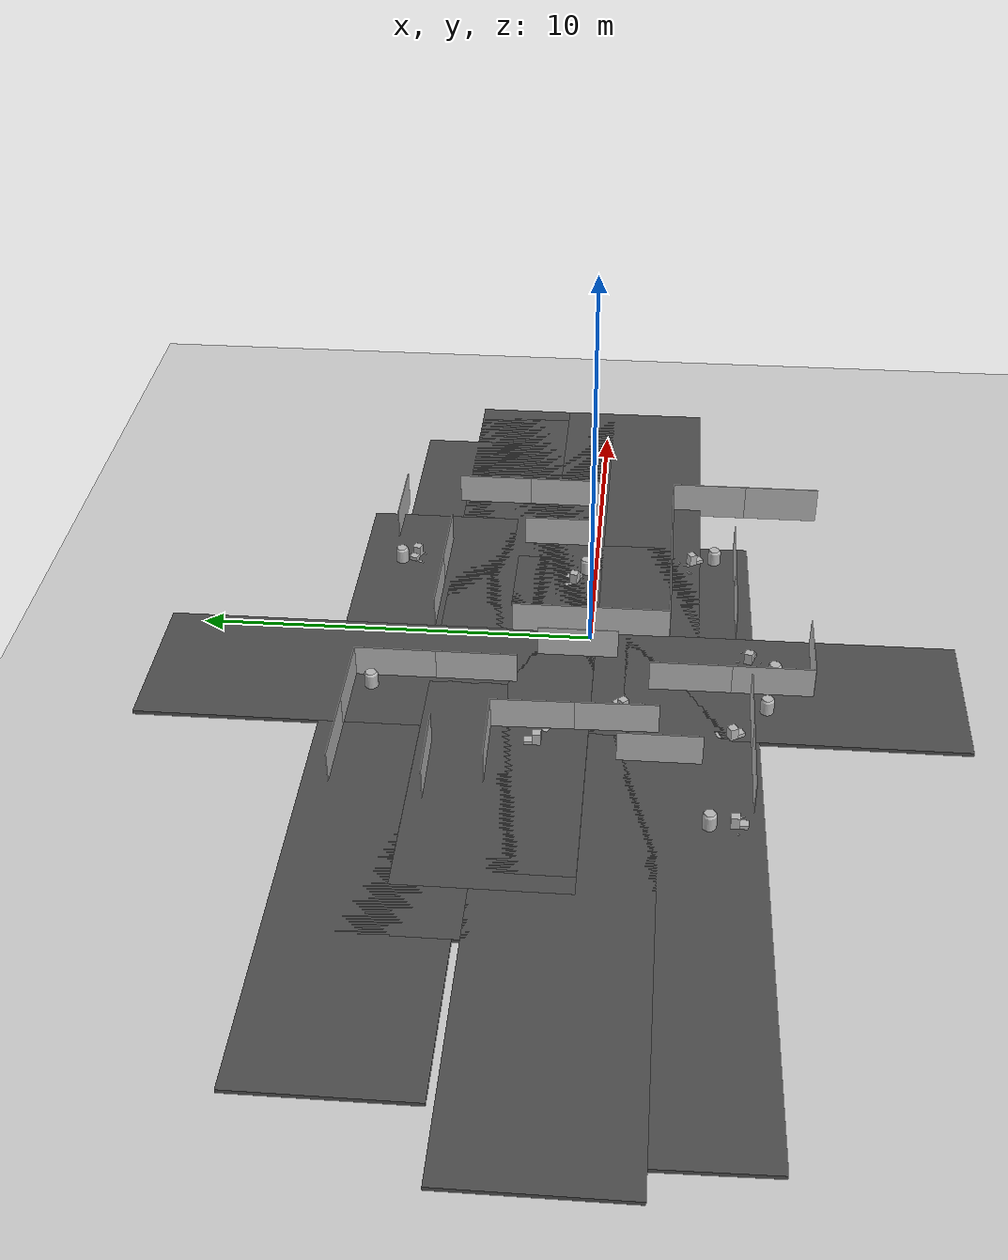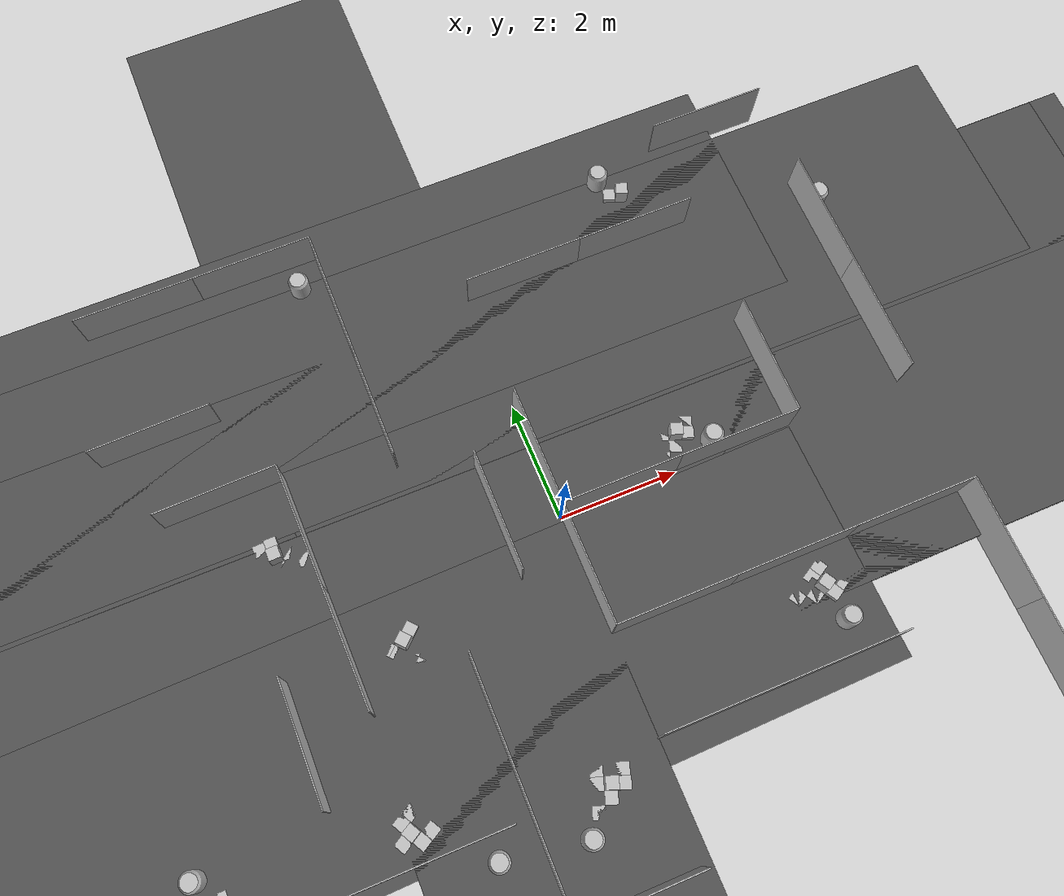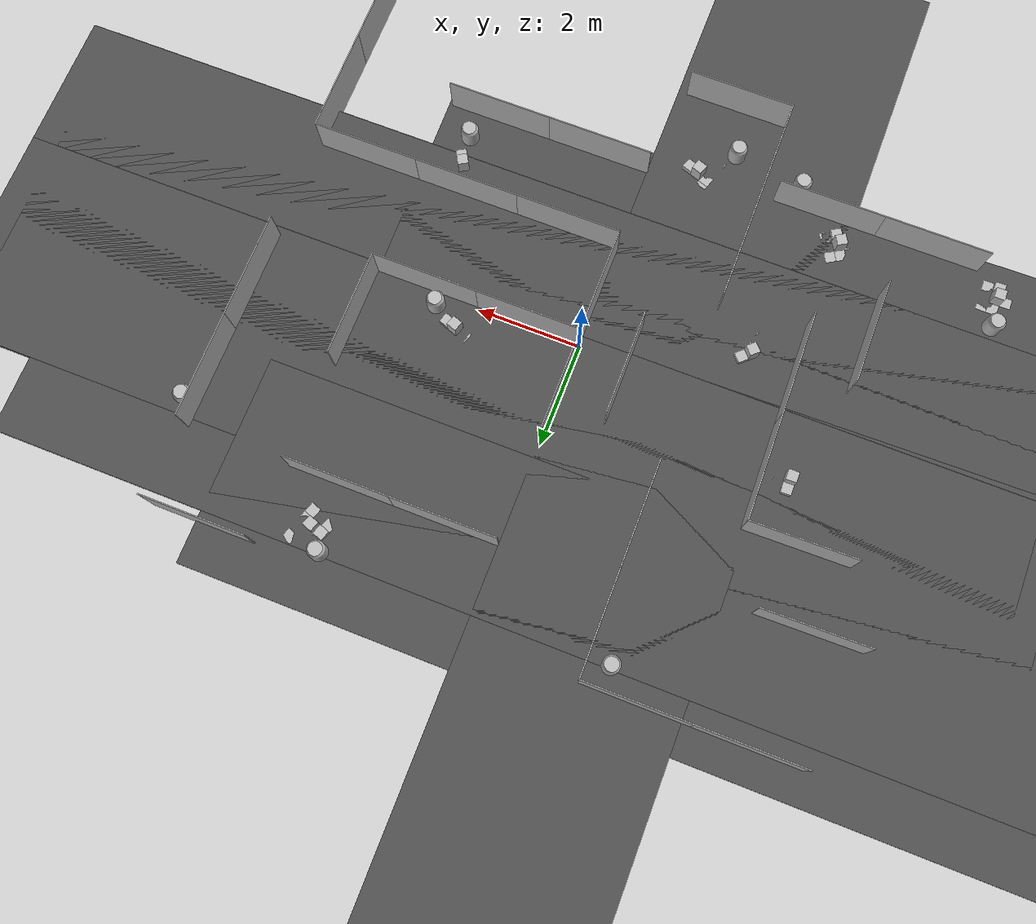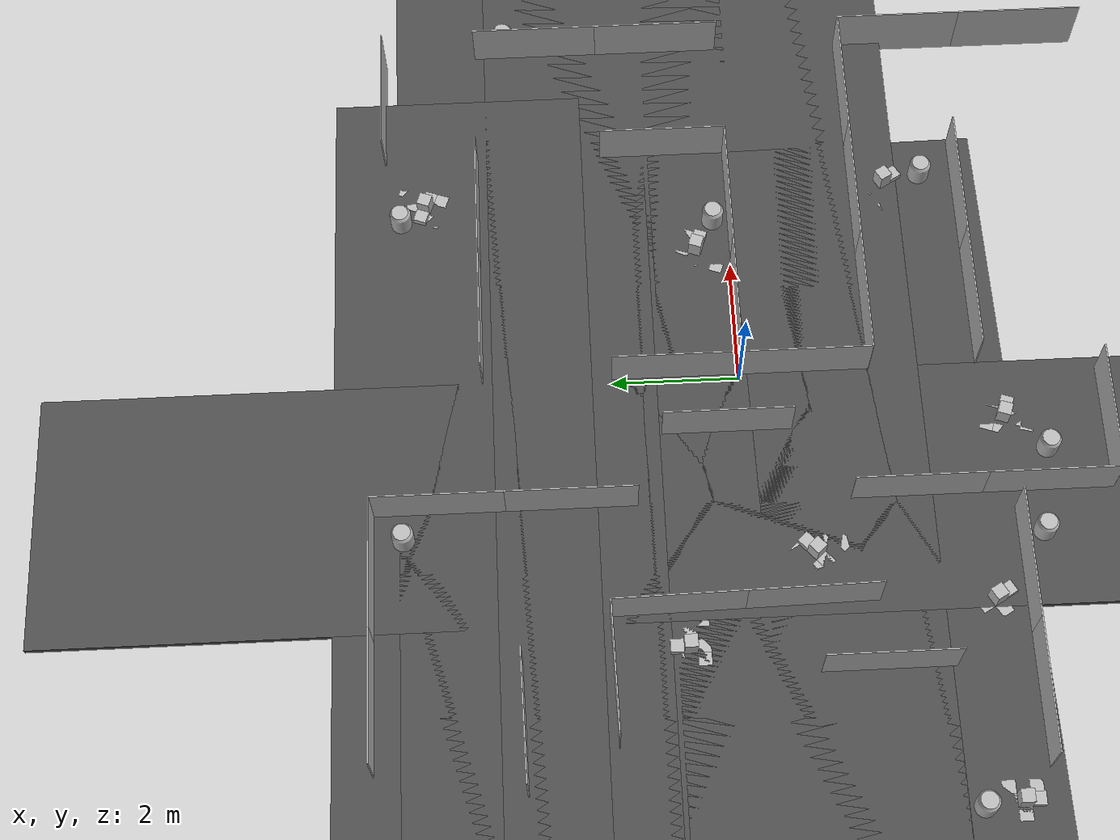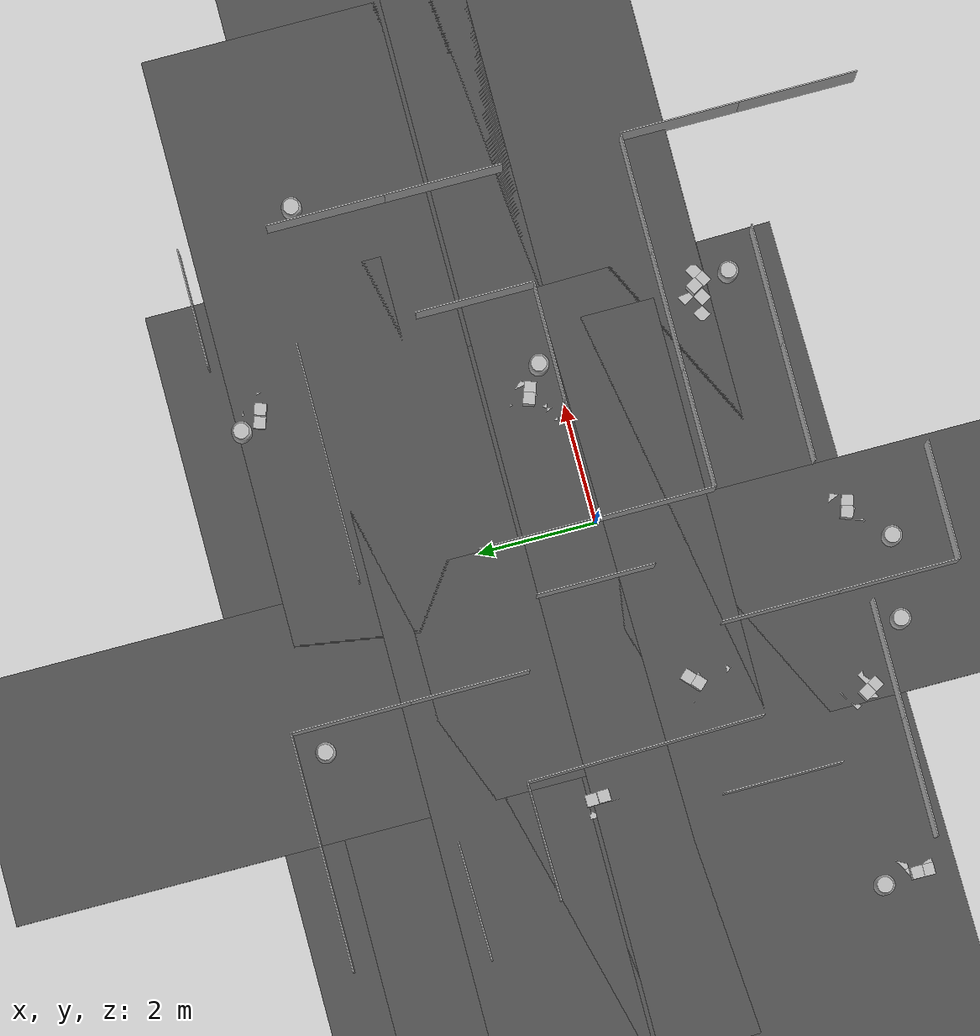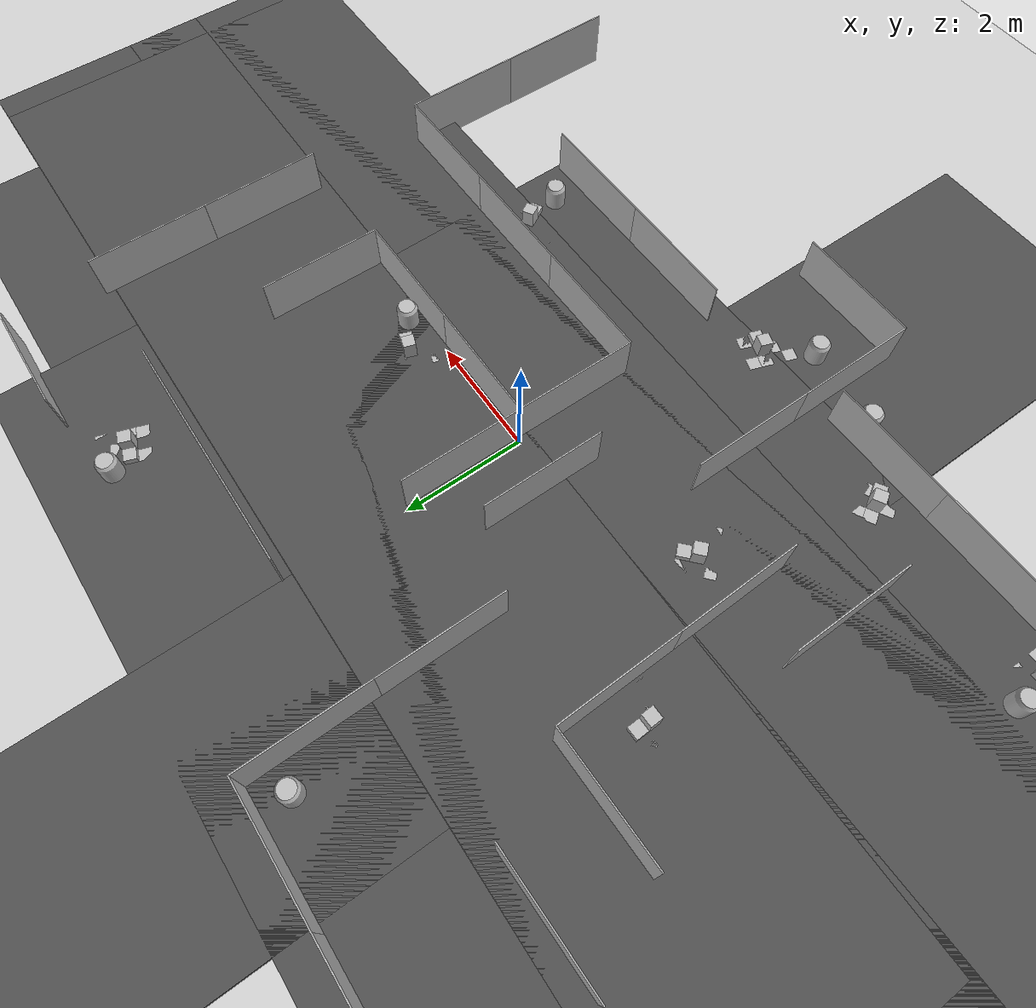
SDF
<sdf version="1.4">
  <!--Generated by blend2world.py-->
  <world name="arena_HKT_18">
    <scene>
      <ambient>0.5 0.5 0.5 1</ambient>
      <background>0.5 0.5 0.5 1</background>
      <shadows>false</shadows>
    </scene>
    <physics type="ode">
      <gravity>0 0 -9.81</gravity>
      <ode>
        <solver>
          <type>quick</type>
          <iters>1000</iters>
          <sor>1.3</sor>
        </solver>
        <constraints>
          <cfm>0.0</cfm>
          <erp>0.2</erp>
          <contact_max_correcting_vel>100.0</contact_max_correcting_vel>
          <contact_surface_layer>0.001</contact_surface_layer>
        </constraints>
      </ode>
      <real_time_update_rate>120</real_time_update_rate>
      <real_time_factor>1</real_time_factor>
      <max_step_size>0.008333</max_step_size>
    </physics>
    <light name="directional_light_1" type="directional">
      <cast_shadows>false</cast_shadows>
      <pose>0 0 30 0.1 0.1 0</pose>
      <diffuse>1.0 1.0 1.0 1</diffuse>
      <specular>.1 .1 .1 1</specular>
      <attenuation>
        <range>300</range>
      </attenuation>
      <direction>0.1 0.1 -1</direction>
    </light>
    <include>
      <uri>model://ground_plane</uri>
    </include>
    <light name="directional_light.-10.0_-12.0" type="sun">
      <pose>-10.0 -12.0 8  0 0 0</pose>
      <cast_shadows>1</cast_shadows>
      <diffuse>0.5 0.5 0.5 1</diffuse>
      <specular>0.1 0.1 0.1 1</specular>
      <attenuation>
        <range>20</range>
        <constant>0.5</constant>
        <linear>0.01</linear>
        <quadratic>0.00</quadratic>
      </attenuation>
      <direction>0.1 0.1 -1.0</direction>
    </light>
    <light name="directional_light.-10.0_0.0" type="sun">
      <pose>-10.0 0.0 8  0 0 0</pose>
      <cast_shadows>1</cast_shadows>
      <diffuse>0.5 0.5 0.5 1</diffuse>
      <specular>0.1 0.1 0.1 1</specular>
      <attenuation>
        <range>20</range>
        <constant>0.5</constant>
        <linear>0.01</linear>
        <quadratic>0.00</quadratic>
      </attenuation>
      <direction>0.1 0.1 -1.0</direction>
    </light>
    <light name="directional_light.-10.0_12.0" type="sun">
      <pose>-10.0 12.0 8  0 0 0</pose>
      <cast_shadows>1</cast_shadows>
      <diffuse>0.5 0.5 0.5 1</diffuse>
      <specular>0.1 0.1 0.1 1</specular>
      <attenuation>
        <range>20</range>
        <constant>0.5</constant>
        <linear>0.01</linear>
        <quadratic>0.00</quadratic>
      </attenuation>
      <direction>0.1 0.1 -1.0</direction>
    </light>
    <light name="directional_light.0.0_-12.0" type="sun">
      <pose>0.0 -12.0 8  0 0 0</pose>
      <cast_shadows>1</cast_shadows>
      <diffuse>0.5 0.5 0.5 1</diffuse>
      <specular>0.1 0.1 0.1 1</specular>
      <attenuation>
        <range>20</range>
        <constant>0.5</constant>
        <linear>0.01</linear>
        <quadratic>0.00</quadratic>
      </attenuation>
      <direction>0.1 0.1 -1.0</direction>
    </light>
    <light name="directional_light.0.0_0.0" type="sun">
      <pose>0.0 0.0 8  0 0 0</pose>
      <cast_shadows>1</cast_shadows>
      <diffuse>0.5 0.5 0.5 1</diffuse>
      <specular>0.1 0.1 0.1 1</specular>
      <attenuation>
        <range>20</range>
        <constant>0.5</constant>
        <linear>0.01</linear>
        <quadratic>0.00</quadratic>
      </attenuation>
      <direction>0.1 0.1 -1.0</direction>
    </light>
    <light name="directional_light.0.0_12.0" type="sun">
      <pose>0.0 12.0 8  0 0 0</pose>
      <cast_shadows>1</cast_shadows>
      <diffuse>0.5 0.5 0.5 1</diffuse>
      <specular>0.1 0.1 0.1 1</specular>
      <attenuation>
        <range>20</range>
        <constant>0.5</constant>
        <linear>0.01</linear>
        <quadratic>0.00</quadratic>
      </attenuation>
      <direction>0.1 0.1 -1.0</direction>
    </light>
    <light name="directional_light.10.0_-12.0" type="sun">
      <pose>10.0 -12.0 8  0 0 0</pose>
      <cast_shadows>1</cast_shadows>
      <diffuse>0.5 0.5 0.5 1</diffuse>
      <specular>0.1 0.1 0.1 1</specular>
      <attenuation>
        <range>20</range>
        <constant>0.5</constant>
        <linear>0.01</linear>
        <quadratic>0.00</quadratic>
      </attenuation>
      <direction>0.1 0.1 -1.0</direction>
    </light>
    <light name="directional_light.10.0_0.0" type="sun">
      <pose>10.0 0.0 8  0 0 0</pose>
      <cast_shadows>1</cast_shadows>
      <diffuse>0.5 0.5 0.5 1</diffuse>
      <specular>0.1 0.1 0.1 1</specular>
      <attenuation>
        <range>20</range>
        <constant>0.5</constant>
        <linear>0.01</linear>
        <quadratic>0.00</quadratic>
      </attenuation>
      <direction>0.1 0.1 -1.0</direction>
    </light>
    <light name="directional_light.10.0_12.0" type="sun">
      <pose>10.0 12.0 8  0 0 0</pose>
      <cast_shadows>1</cast_shadows>
      <diffuse>0.5 0.5 0.5 1</diffuse>
      <specular>0.1 0.1 0.1 1</specular>
      <attenuation>
        <range>20</range>
        <constant>0.5</constant>
        <linear>0.01</linear>
        <quadratic>0.00</quadratic>
      </attenuation>
      <direction>0.1 0.1 -1.0</direction>
    </light>
    <include>
      <name>barrel_110l.136</name>
      <pose>-6.941155910491943 -2.995645046234131 0.0  0.0 0.0 0.0</pose>
      <uri>model://barrel_110l</uri>
    </include>
    <include>
      <name>barrel_110l.137</name>
      <pose>-2.538693428039551 5.237995624542236 0.0  0.0 0.0 0.0</pose>
      <uri>model://barrel_110l</uri>
    </include>
    <include>
      <name>barrel_110l.138</name>
      <pose>2.890841007232666 5.237995624542236 0.0  0.0 0.0 0.0</pose>
      <uri>model://barrel_110l</uri>
    </include>
    <include>
      <name>barrel_110l.139</name>
      <pose>3.415881633758545 -3.143953323364258 0.0  0.0 0.0 0.0</pose>
      <uri>model://barrel_110l</uri>
    </include>
    <include>
      <name>barrel_110l.140</name>
      <pose>-2.8183698654174805 -4.385210990905762 0.0  0.0 0.0 0.0</pose>
      <uri>model://barrel_110l</uri>
    </include>
    <include>
      <name>barrel_110l.141</name>
      <pose>6.263016223907471 3.5188968181610107 0.0  0.0 0.0 0.0</pose>
      <uri>model://barrel_110l</uri>
    </include>
    <include>
      <name>barrel_110l.142</name>
      <pose>2.723001718521118 0.25193217396736145 0.0  0.0 0.0 0.0</pose>
      <uri>model://barrel_110l</uri>
    </include>
    <include>
      <name>barrel_110l.143</name>
      <pose>-1.4703285694122314 -4.603447914123535 0.0  0.0 0.0 0.0</pose>
      <uri>model://barrel_110l</uri>
    </include>
    <include>
      <name>cube_20x20.1794</name>
      <pose>-4.375776290893555 0.8407224416732788 0.10000000149011612  0.0 -0.0 6.301559925079346</pose>
      <uri>model://cube_20x20</uri>
    </include>
    <include>
      <name>cube_20x20.1795</name>
      <pose>-4.179484844207764 1.044363260269165 0.10000000149011612  0.0 -0.0 6.301559925079346</pose>
      <uri>model://cube_20x20</uri>
    </include>
    <include>
      <name>cube_20x20.1796</name>
      <pose>-3.975843906402588 0.8480718731880188 0.10000000149011612  0.0 -0.0 6.301559925079346</pose>
      <uri>model://cube_20x20</uri>
    </include>
    <include>
      <name>cube_20x20.1797</name>
      <pose>-4.575742721557617 0.8370477557182312 0.10000000149011612  0.0 -0.0 6.301559925079346</pose>
      <uri>model://cube_20x20</uri>
    </include>
    <include>
      <name>cube_20x20.1798</name>
      <pose>-4.583092212677002 1.2369798421859741 0.10000000149011612  0.0 -0.0 6.301559925079346</pose>
      <uri>model://cube_20x20</uri>
    </include>
    <include>
      <name>cube_20x20.1799</name>
      <pose>-4.375776290893555 0.8407224416732788 0.10000000149011612  0.0 -0.0 6.301559925079346</pose>
      <uri>model://cube_20x20</uri>
    </include>
    <include>
      <name>cube_20x20.1800</name>
      <pose>-4.179484844207764 1.044363260269165 0.10000000149011612  0.0 -0.0 6.301559925079346</pose>
      <uri>model://cube_20x20</uri>
    </include>
    <include>
      <name>cube_20x20.1801</name>
      <pose>-3.975843906402588 0.8480718731880188 0.10000000149011612  0.0 -0.0 6.301559925079346</pose>
      <uri>model://cube_20x20</uri>
    </include>
    <include>
      <name>cube_20x20.1802</name>
      <pose>-4.575742721557617 0.8370477557182312 0.10000000149011612  0.0 -0.0 6.301559925079346</pose>
      <uri>model://cube_20x20</uri>
    </include>
    <include>
      <name>cube_20x20.1803</name>
      <pose>-4.583092212677002 1.2369798421859741 0.10000000149011612  0.0 -0.0 6.301559925079346</pose>
      <uri>model://cube_20x20</uri>
    </include>
    <include>
      <name>cube_20x20.1804</name>
      <pose>-6.874878406524658 -3.3630831241607666 0.10000000149011612  0.0 -0.0 3.141592502593994</pose>
      <uri>model://cube_20x20</uri>
    </include>
    <include>
      <name>cube_20x20.1805</name>
      <pose>-7.074878215789795 -3.5630829334259033 0.10000000149011612  0.0 -0.0 3.141592502593994</pose>
      <uri>model://cube_20x20</uri>
    </include>
    <include>
      <name>cube_20x20.1806</name>
      <pose>-6.674878120422363 -3.3630831241607666 0.10000000149011612  0.0 -0.0 3.141592502593994</pose>
      <uri>model://cube_20x20</uri>
    </include>
    <include>
      <name>cube_20x20.1807</name>
      <pose>-6.674878120422363 -3.76308274269104 0.10000000149011612  0.0 -0.0 3.141592502593994</pose>
      <uri>model://cube_20x20</uri>
    </include>
    <include>
      <name>cube_20x20.1808</name>
      <pose>-6.874878406524658 -3.3630831241607666 0.10000000149011612  0.0 -0.0 3.141592502593994</pose>
      <uri>model://cube_20x20</uri>
    </include>
    <include>
      <name>cube_20x20.1809</name>
      <pose>-7.074878215789795 -3.5630829334259033 0.10000000149011612  0.0 -0.0 3.141592502593994</pose>
      <uri>model://cube_20x20</uri>
    </include>
    <include>
      <name>cube_20x20.1810</name>
      <pose>-6.674878120422363 -3.3630831241607666 0.10000000149011612  0.0 -0.0 3.141592502593994</pose>
      <uri>model://cube_20x20</uri>
    </include>
    <include>
      <name>cube_20x20.1811</name>
      <pose>-6.674878120422363 -3.76308274269104 0.10000000149011612  0.0 -0.0 3.141592502593994</pose>
      <uri>model://cube_20x20</uri>
    </include>
    <include>
      <name>cube_20x20.1812</name>
      <pose>-3.9385533332824707 -3.3717634677886963 0.10000000149011612  0.0 -0.0 3.6651763916015625</pose>
      <uri>model://cube_20x20</uri>
    </include>
    <include>
      <name>cube_20x20.1813</name>
      <pose>-4.011762619018555 -3.6449673175811768 0.10000000149011612  0.0 -0.0 3.6651763916015625</pose>
      <uri>model://cube_20x20</uri>
    </include>
    <include>
      <name>cube_20x20.1814</name>
      <pose>-3.7653465270996094 -3.271765947341919 0.10000000149011612  0.0 -0.0 3.6651763916015625</pose>
      <uri>model://cube_20x20</uri>
    </include>
    <include>
      <name>cube_20x20.1815</name>
      <pose>-3.565351963043213 -3.6181790828704834 0.10000000149011612  0.0 -0.0 3.6651763916015625</pose>
      <uri>model://cube_20x20</uri>
    </include>
    <include>
      <name>cube_20x20.1816</name>
      <pose>-3.9385533332824707 -3.3717634677886963 0.10000000149011612  0.0 -0.0 3.6651763916015625</pose>
      <uri>model://cube_20x20</uri>
    </include>
    <include>
      <name>cube_20x20.1817</name>
      <pose>-4.011762619018555 -3.6449673175811768 0.10000000149011612  0.0 -0.0 3.6651763916015625</pose>
      <uri>model://cube_20x20</uri>
    </include>
    <include>
      <name>cube_20x20.1818</name>
      <pose>-3.7653465270996094 -3.271765947341919 0.10000000149011612  0.0 -0.0 3.6651763916015625</pose>
      <uri>model://cube_20x20</uri>
    </include>
    <include>
      <name>cube_20x20.1819</name>
      <pose>-3.565351963043213 -3.6181790828704834 0.10000000149011612  0.0 -0.0 3.6651763916015625</pose>
      <uri>model://cube_20x20</uri>
    </include>
    <include>
      <name>cube_20x20.1820</name>
      <pose>-3.1368727684020996 -1.071094274520874 0.10000000149011612  0.0 0.0 5.4528021812438965</pose>
      <uri>model://cube_20x20</uri>
    </include>
    <include>
      <name>cube_20x20.1821</name>
      <pose>-2.8543167114257812 -1.0838134288787842 0.10000000149011612  0.0 0.0 5.4528021812438965</pose>
      <uri>model://cube_20x20</uri>
    </include>
    <include>
      <name>cube_20x20.1822</name>
      <pose>-2.8670363426208496 -1.3663697242736816 0.10000000149011612  0.0 0.0 5.4528021812438965</pose>
      <uri>model://cube_20x20</uri>
    </include>
    <include>
      <name>cube_20x20.1823</name>
      <pose>-3.2717912197113037 -0.9234559535980225 0.10000000149011612  0.0 0.0 5.4528021812438965</pose>
      <uri>model://cube_20x20</uri>
    </include>
    <include>
      <name>cube_20x20.1824</name>
      <pose>-2.976515293121338 -0.6536192893981934 0.10000000149011612  0.0 0.0 5.4528021812438965</pose>
      <uri>model://cube_20x20</uri>
    </include>
    <include>
      <name>cube_20x20.1825</name>
      <pose>-3.1368727684020996 -1.071094274520874 0.10000000149011612  0.0 0.0 5.4528021812438965</pose>
      <uri>model://cube_20x20</uri>
    </include>
    <include>
      <name>cube_20x20.1826</name>
      <pose>-2.8543167114257812 -1.0838134288787842 0.10000000149011612  0.0 0.0 5.4528021812438965</pose>
      <uri>model://cube_20x20</uri>
    </include>
    <include>
      <name>cube_20x20.1827</name>
      <pose>-2.8670363426208496 -1.3663697242736816 0.10000000149011612  0.0 0.0 5.4528021812438965</pose>
      <uri>model://cube_20x20</uri>
    </include>
    <include>
      <name>cube_20x20.1828</name>
      <pose>-3.2717912197113037 -0.9234559535980225 0.10000000149011612  0.0 0.0 5.4528021812438965</pose>
      <uri>model://cube_20x20</uri>
    </include>
    <include>
      <name>cube_20x20.1829</name>
      <pose>-2.976515293121338 -0.6536192893981934 0.10000000149011612  0.0 0.0 5.4528021812438965</pose>
      <uri>model://cube_20x20</uri>
    </include>
    <include>
      <name>cube_20x30.331</name>
      <pose>-4.383125305175781 1.2406545877456665 0.15000000596046448  0.0 -0.0 6.301559925079346</pose>
      <uri>model://cube_20x30</uri>
    </include>
    <include>
      <name>cube_20x30.332</name>
      <pose>-4.383125305175781 1.2406545877456665 0.15000000596046448  0.0 -0.0 6.301559925079346</pose>
      <uri>model://cube_20x30</uri>
    </include>
    <include>
      <name>cube_20x30.333</name>
      <pose>-6.874878406524658 -3.76308274269104 0.15000000596046448  0.0 -0.0 3.141592502593994</pose>
      <uri>model://cube_20x30</uri>
    </include>
    <include>
      <name>cube_20x30.334</name>
      <pose>-6.874878406524658 -3.76308274269104 0.15000000596046448  0.0 -0.0 3.141592502593994</pose>
      <uri>model://cube_20x30</uri>
    </include>
    <include>
      <name>cube_20x30.335</name>
      <pose>-3.738558769226074 -3.7181766033172607 0.15000000596046448  0.0 -0.0 3.6651763916015625</pose>
      <uri>model://cube_20x30</uri>
    </include>
    <include>
      <name>cube_20x30.336</name>
      <pose>-3.738558769226074 -3.7181766033172607 0.15000000596046448  0.0 -0.0 3.6651763916015625</pose>
      <uri>model://cube_20x30</uri>
    </include>
    <include>
      <name>cube_20x30.337</name>
      <pose>-2.841596841812134 -0.8012573719024658 0.15000000596046448  0.0 0.0 5.4528021812438965</pose>
      <uri>model://cube_20x30</uri>
    </include>
    <include>
      <name>cube_20x30.338</name>
      <pose>-2.841596841812134 -0.8012573719024658 0.15000000596046448  0.0 0.0 5.4528021812438965</pose>
      <uri>model://cube_20x30</uri>
    </include>
    <include>
      <name>cube_20x50.325</name>
      <pose>-4.379450798034668 1.0406885147094727 0.25  0.0 -0.0 6.301559925079346</pose>
      <uri>model://cube_20x50</uri>
    </include>
    <include>
      <name>cube_20x50.326</name>
      <pose>-4.379450798034668 1.0406885147094727 0.25  0.0 -0.0 6.301559925079346</pose>
      <uri>model://cube_20x50</uri>
    </include>
    <include>
      <name>cube_20x50.327</name>
      <pose>-6.874878406524658 -3.5630829334259033 0.25  0.0 -0.0 3.141592502593994</pose>
      <uri>model://cube_20x50</uri>
    </include>
    <include>
      <name>cube_20x50.328</name>
      <pose>-6.874878406524658 -3.5630829334259033 0.25  0.0 -0.0 3.141592502593994</pose>
      <uri>model://cube_20x50</uri>
    </include>
    <include>
      <name>cube_20x50.329</name>
      <pose>-3.8385560512542725 -3.5449702739715576 0.25  0.0 -0.0 3.6651763916015625</pose>
      <uri>model://cube_20x50</uri>
    </include>
    <include>
      <name>cube_20x50.330</name>
      <pose>-3.8385560512542725 -3.5449702739715576 0.25  0.0 -0.0 3.6651763916015625</pose>
      <uri>model://cube_20x50</uri>
    </include>
    <include>
      <name>cube_20x50.331</name>
      <pose>-2.989234209060669 -0.9361758232116699 0.25  0.0 0.0 5.4528021812438965</pose>
      <uri>model://cube_20x50</uri>
    </include>
    <include>
      <name>cube_20x50.332</name>
      <pose>-2.989234209060669 -0.9361758232116699 0.25  0.0 0.0 5.4528021812438965</pose>
      <uri>model://cube_20x50</uri>
    </include>
    <include>
      <name>ramp.163</name>
      <pose>-1.982873558998108 0.8252742290496826 0.15000000596046448  0.0 -0.0 7.853981971740723</pose>
      <uri>model://ramp</uri>
    </include>
    <include>
      <name>ramp.164</name>
      <pose>-5.96612548828125 -2.2167935371398926 0.15000000596046448  0.0 -0.0 9.44315242767334</pose>
      <uri>model://ramp</uri>
    </include>
    <include>
      <name>ramp.165</name>
      <pose>-6.66489315032959 0.13354206085205078 0.15000000596046448  0.0 -0.0 6.283185005187988</pose>
      <uri>model://ramp</uri>
    </include>
    <include>
      <name>ramp.166</name>
      <pose>-4.8568115234375 4.303653717041016 0.15000000596046448  0.0 -0.0 6.283185005187988</pose>
      <uri>model://ramp</uri>
    </include>
    <include>
      <name>wall_2x1.708</name>
      <pose>-3.801290512084961 -0.8092706203460693 0.5130000114440918  0.0 -0.0 4.7307634353637695</pose>
      <uri>model://wall_2x1</uri>
    </include>
    <include>
      <name>wall_2x1.709</name>
      <pose>-5.502535343170166 3.501715660095215 0.5130000114440918  0.0 -0.0 3.1599674224853516</pose>
      <uri>model://wall_2x1</uri>
    </include>
    <include>
      <name>wall_stand.1537</name>
      <pose>-1.8005000352859497 2.0 0.03449999913573265  0.0 -0.0 1.570796251296997</pose>
      <uri>model://wall_stand</uri>
    </include>
    <include>
      <name>wall_stand.1538</name>
      <pose>-0.19949999451637268 2.0 0.03449999913573265  0.0 -0.0 1.570796251296997</pose>
      <uri>model://wall_stand</uri>
    </include>
    <include>
      <name>wall_2x1.710</name>
      <pose>-3.8380374908447266 1.1903918981552124 0.5130000114440918  0.0 -0.0 4.7307634353637695</pose>
      <uri>model://wall_2x1</uri>
    </include>
    <include>
      <name>wall_2x1.711</name>
      <pose>-4.8562421798706055 2.1718497276306152 0.5130000114440918  0.0 -0.0 3.1599674224853516</pose>
      <uri>model://wall_2x1</uri>
    </include>
    <include>
      <name>wall_stand.1539</name>
      <pose>-0.19949999451637268 2.0 0.03449999913573265  0.0 -0.0 1.570796251296997</pose>
      <uri>model://wall_stand</uri>
    </include>
    <include>
      <name>wall_2x1.712</name>
      <pose>-2.147331953048706 -2.5302858352661133 0.5130000114440918  0.0 -0.0 1.570796251296997</pose>
      <uri>model://wall_2x1</uri>
    </include>
    <include>
      <name>wall_stand.1540</name>
      <pose>-1.8005000352859497 2.0 0.03449999913573265  0.0 -0.0 1.570796251296997</pose>
      <uri>model://wall_stand</uri>
    </include>
    <include>
      <name>wall_stand.1541</name>
      <pose>-0.19949999451637268 2.0 0.03449999913573265  0.0 -0.0 1.570796251296997</pose>
      <uri>model://wall_stand</uri>
    </include>
    <include>
      <name>wall_2x1.713</name>
      <pose>-1.1473321914672852 -5.530285835266113 0.5130000114440918  0.0 -0.0 3.141592502593994</pose>
      <uri>model://wall_2x1</uri>
    </include>
    <include>
      <name>wall_2x1.714</name>
      <pose>-2.147332191467285 -4.530285835266113 0.5130000114440918  0.0 -0.0 1.570796251296997</pose>
      <uri>model://wall_2x1</uri>
    </include>
    <include>
      <name>wall_stand.1542</name>
      <pose>-0.19949999451637268 2.0 0.03449999913573265  0.0 -0.0 1.570796251296997</pose>
      <uri>model://wall_stand</uri>
    </include>
    <include>
      <name>wall_2x1.715</name>
      <pose>-2.1166141033172607 2.695002794265747 0.5130000114440918  0.0 -0.0 4.71238899230957</pose>
      <uri>model://wall_2x1</uri>
    </include>
    <include>
      <name>wall_stand.1543</name>
      <pose>-1.8005000352859497 2.0 0.03449999913573265  0.0 -0.0 1.570796251296997</pose>
      <uri>model://wall_stand</uri>
    </include>
    <include>
      <name>wall_stand.1544</name>
      <pose>-0.19949999451637268 2.0 0.03449999913573265  0.0 -0.0 1.570796251296997</pose>
      <uri>model://wall_stand</uri>
    </include>
    <include>
      <name>wall_2x1.716</name>
      <pose>-5.116613388061523 5.695002555847168 0.5130000114440918  0.0 -0.0 6.283185005187988</pose>
      <uri>model://wall_2x1</uri>
    </include>
    <include>
      <name>wall_2x1.717</name>
      <pose>-3.1166136264801025 5.695002555847168 0.5130000114440918  0.0 -0.0 6.283185005187988</pose>
      <uri>model://wall_2x1</uri>
    </include>
    <include>
      <name>wall_2x1.718</name>
      <pose>-2.1166136264801025 4.695002555847168 0.5130000114440918  0.0 -0.0 4.71238899230957</pose>
      <uri>model://wall_2x1</uri>
    </include>
    <include>
      <name>wall_stand.1545</name>
      <pose>-0.19949999451637268 2.0 0.03449999913573265  0.0 -0.0 1.570796251296997</pose>
      <uri>model://wall_stand</uri>
    </include>
    <include>
      <name>wall_2x1.719</name>
      <pose>-0.958229660987854 0.2739219665527344 0.5130000114440918  0.0 -0.0 4.71238899230957</pose>
      <uri>model://wall_2x1</uri>
    </include>
    <include>
      <name>wall_stand.1546</name>
      <pose>-1.8005000352859497 2.0 0.03449999913573265  0.0 -0.0 1.570796251296997</pose>
      <uri>model://wall_stand</uri>
    </include>
    <include>
      <name>wall_stand.1547</name>
      <pose>-0.19949999451637268 2.0 0.03449999913573265  0.0 -0.0 1.570796251296997</pose>
      <uri>model://wall_stand</uri>
    </include>
    <include>
      <name>wall_stand.1548</name>
      <pose>-3.7865824699401855 -1.609635353088379 0.03450000286102295  0.0 -0.0 3.1599674224853516</pose>
      <uri>model://wall_stand</uri>
    </include>
    <include>
      <name>wall_stand.1549</name>
      <pose>-3.815998077392578 -0.008905649185180664 0.03450000286102295  0.0 -0.0 3.1599674224853516</pose>
      <uri>model://wall_stand</uri>
    </include>
    <include>
      <name>wall_stand.1550</name>
      <pose>-3.823329448699951 0.39002686738967896 0.03450000286102295  0.0 -0.0 3.1599674224853516</pose>
      <uri>model://wall_stand</uri>
    </include>
    <include>
      <name>wall_stand.1551</name>
      <pose>-3.8527450561523438 1.9907567501068115 0.03450000286102295  0.0 -0.0 3.1599674224853516</pose>
      <uri>model://wall_stand</uri>
    </include>
    <include>
      <name>wall_stand.1552</name>
      <pose>-2.346832275390625 -5.530285835266113 0.03450000286102295  0.0 -0.0 1.570796251296997</pose>
      <uri>model://wall_stand</uri>
    </include>
    <include>
      <name>wall_stand.1553</name>
      <pose>-5.917113304138184 5.695002555847168 0.03450000286102295  0.0 -0.0 4.71238899230957</pose>
      <uri>model://wall_stand</uri>
    </include>
    <include>
      <name>wall_stand.1554</name>
      <pose>-4.316113471984863 5.695002555847168 0.03450000286102295  0.0 -0.0 4.71238899230957</pose>
      <uri>model://wall_stand</uri>
    </include>
    <include>
      <name>wall_stand.1555</name>
      <pose>-2.316113233566284 5.695002555847168 0.03450000286102295  0.0 -0.0 4.71238899230957</pose>
      <uri>model://wall_stand</uri>
    </include>
    <include>
      <name>wall_stand.1556</name>
      <pose>-3.9171135425567627 5.695002555847168 0.03450000286102295  0.0 -0.0 4.71238899230957</pose>
      <uri>model://wall_stand</uri>
    </include>
    <include>
      <name>cube_20x20.1830</name>
      <pose>2.0343916416168213 0.613365888595581 0.10000000149011612  0.0 0.0 4.376082897186279</pose>
      <uri>model://cube_20x20</uri>
    </include>
    <include>
      <name>cube_20x20.1831</name>
      <pose>2.1571874618530273 0.358569860458374 0.10000000149011612  0.0 0.0 4.376082897186279</pose>
      <uri>model://cube_20x20</uri>
    </include>
    <include>
      <name>cube_20x20.1832</name>
      <pose>1.902390956878662 0.23577475547790527 0.10000000149011612  0.0 0.0 4.376082897186279</pose>
      <uri>model://cube_20x20</uri>
    </include>
    <include>
      <name>cube_20x20.1833</name>
      <pose>2.1003925800323486 0.8021619319915771 0.10000000149011612  0.0 0.0 4.376082897186279</pose>
      <uri>model://cube_20x20</uri>
    </include>
    <include>
      <name>cube_20x20.1834</name>
      <pose>2.4779841899871826 0.6701610088348389 0.10000000149011612  0.0 0.0 4.376082897186279</pose>
      <uri>model://cube_20x20</uri>
    </include>
    <include>
      <name>cube_20x20.1835</name>
      <pose>2.0343916416168213 0.613365888595581 0.10000000149011612  0.0 0.0 4.376082897186279</pose>
      <uri>model://cube_20x20</uri>
    </include>
    <include>
      <name>cube_20x20.1836</name>
      <pose>2.1571874618530273 0.358569860458374 0.10000000149011612  0.0 0.0 4.376082897186279</pose>
      <uri>model://cube_20x20</uri>
    </include>
    <include>
      <name>cube_20x20.1837</name>
      <pose>1.902390956878662 0.23577475547790527 0.10000000149011612  0.0 0.0 4.376082897186279</pose>
      <uri>model://cube_20x20</uri>
    </include>
    <include>
      <name>cube_20x20.1838</name>
      <pose>2.1003925800323486 0.8021619319915771 0.10000000149011612  0.0 0.0 4.376082897186279</pose>
      <uri>model://cube_20x20</uri>
    </include>
    <include>
      <name>cube_20x20.1839</name>
      <pose>2.4779841899871826 0.6701610088348389 0.10000000149011612  0.0 0.0 4.376082897186279</pose>
      <uri>model://cube_20x20</uri>
    </include>
    <include>
      <name>cube_20x20.1840</name>
      <pose>3.3604865074157715 4.783919334411621 0.10000000149011612  0.0 0.0 7.517675399780273</pose>
      <uri>model://cube_20x20</uri>
    </include>
    <include>
      <name>cube_20x20.1841</name>
      <pose>3.2376906871795654 5.038715362548828 0.10000000149011612  0.0 0.0 7.517675399780273</pose>
      <uri>model://cube_20x20</uri>
    </include>
    <include>
      <name>cube_20x20.1842</name>
      <pose>3.4924871921539307 5.161510944366455 0.10000000149011612  0.0 0.0 7.517675399780273</pose>
      <uri>model://cube_20x20</uri>
    </include>
    <include>
      <name>cube_20x20.1843</name>
      <pose>3.294485569000244 4.595123291015625 0.10000000149011612  0.0 0.0 7.517675399780273</pose>
      <uri>model://cube_20x20</uri>
    </include>
    <include>
      <name>cube_20x20.1844</name>
      <pose>2.91689395904541 4.727124214172363 0.10000000149011612  0.0 0.0 7.517675399780273</pose>
      <uri>model://cube_20x20</uri>
    </include>
    <include>
      <name>cube_20x20.1845</name>
      <pose>3.3604865074157715 4.783919334411621 0.10000000149011612  0.0 0.0 7.517675399780273</pose>
      <uri>model://cube_20x20</uri>
    </include>
    <include>
      <name>cube_20x20.1846</name>
      <pose>3.2376906871795654 5.038715362548828 0.10000000149011612  0.0 0.0 7.517675399780273</pose>
      <uri>model://cube_20x20</uri>
    </include>
    <include>
      <name>cube_20x20.1847</name>
      <pose>3.4924871921539307 5.161510944366455 0.10000000149011612  0.0 0.0 7.517675399780273</pose>
      <uri>model://cube_20x20</uri>
    </include>
    <include>
      <name>cube_20x20.1848</name>
      <pose>3.294485569000244 4.595123291015625 0.10000000149011612  0.0 0.0 7.517675399780273</pose>
      <uri>model://cube_20x20</uri>
    </include>
    <include>
      <name>cube_20x20.1849</name>
      <pose>2.91689395904541 4.727124214172363 0.10000000149011612  0.0 0.0 7.517675399780273</pose>
      <uri>model://cube_20x20</uri>
    </include>
    <include>
      <name>cube_20x20.1850</name>
      <pose>3.2194247245788574 -2.3717634677886963 0.10000000149011612  0.0 -0.0 3.6651763916015625</pose>
      <uri>model://cube_20x20</uri>
    </include>
    <include>
      <name>cube_20x20.1851</name>
      <pose>3.1462156772613525 -2.6449673175811768 0.10000000149011612  0.0 -0.0 3.6651763916015625</pose>
      <uri>model://cube_20x20</uri>
    </include>
    <include>
      <name>cube_20x20.1852</name>
      <pose>2.873011827468872 -2.5717580318450928 0.10000000149011612  0.0 -0.0 3.6651763916015625</pose>
      <uri>model://cube_20x20</uri>
    </include>
    <include>
      <name>cube_20x20.1853</name>
      <pose>3.3926315307617188 -2.271765947341919 0.10000000149011612  0.0 -0.0 3.6651763916015625</pose>
      <uri>model://cube_20x20</uri>
    </include>
    <include>
      <name>cube_20x20.1854</name>
      <pose>3.5926260948181152 -2.6181790828704834 0.10000000149011612  0.0 -0.0 3.6651763916015625</pose>
      <uri>model://cube_20x20</uri>
    </include>
    <include>
      <name>cube_20x20.1855</name>
      <pose>3.2194247245788574 -2.3717634677886963 0.10000000149011612  0.0 -0.0 3.6651763916015625</pose>
      <uri>model://cube_20x20</uri>
    </include>
    <include>
      <name>cube_20x20.1856</name>
      <pose>3.1462156772613525 -2.6449673175811768 0.10000000149011612  0.0 -0.0 3.6651763916015625</pose>
      <uri>model://cube_20x20</uri>
    </include>
    <include>
      <name>cube_20x20.1857</name>
      <pose>2.873011827468872 -2.5717580318450928 0.10000000149011612  0.0 -0.0 3.6651763916015625</pose>
      <uri>model://cube_20x20</uri>
    </include>
    <include>
      <name>cube_20x20.1858</name>
      <pose>3.3926315307617188 -2.271765947341919 0.10000000149011612  0.0 -0.0 3.6651763916015625</pose>
      <uri>model://cube_20x20</uri>
    </include>
    <include>
      <name>cube_20x20.1859</name>
      <pose>3.5926260948181152 -2.6181790828704834 0.10000000149011612  0.0 -0.0 3.6651763916015625</pose>
      <uri>model://cube_20x20</uri>
    </include>
    <include>
      <name>cube_20x20.1860</name>
      <pose>-1.094416618347168 -3.9300127029418945 0.10000000149011612  0.0 0.0 4.376082897186279</pose>
      <uri>model://cube_20x20</uri>
    </include>
    <include>
      <name>cube_20x20.1861</name>
      <pose>-0.9716207981109619 -4.184808731079102 0.10000000149011612  0.0 0.0 4.376082897186279</pose>
      <uri>model://cube_20x20</uri>
    </include>
    <include>
      <name>cube_20x20.1862</name>
      <pose>-1.2264173030853271 -4.307604789733887 0.10000000149011612  0.0 0.0 4.376082897186279</pose>
      <uri>model://cube_20x20</uri>
    </include>
    <include>
      <name>cube_20x20.1863</name>
      <pose>-1.0284156799316406 -3.7412166595458984 0.10000000149011612  0.0 0.0 4.376082897186279</pose>
      <uri>model://cube_20x20</uri>
    </include>
    <include>
      <name>cube_20x20.1864</name>
      <pose>-0.6508240699768066 -3.8732175827026367 0.10000000149011612  0.0 0.0 4.376082897186279</pose>
      <uri>model://cube_20x20</uri>
    </include>
    <include>
      <name>cube_20x20.1865</name>
      <pose>-1.094416618347168 -3.9300127029418945 0.10000000149011612  0.0 0.0 4.376082897186279</pose>
      <uri>model://cube_20x20</uri>
    </include>
    <include>
      <name>cube_20x20.1866</name>
      <pose>-0.9716207981109619 -4.184808731079102 0.10000000149011612  0.0 0.0 4.376082897186279</pose>
      <uri>model://cube_20x20</uri>
    </include>
    <include>
      <name>cube_20x20.1867</name>
      <pose>-1.2264173030853271 -4.307604789733887 0.10000000149011612  0.0 0.0 4.376082897186279</pose>
      <uri>model://cube_20x20</uri>
    </include>
    <include>
      <name>cube_20x20.1868</name>
      <pose>-1.0284156799316406 -3.7412166595458984 0.10000000149011612  0.0 0.0 4.376082897186279</pose>
      <uri>model://cube_20x20</uri>
    </include>
    <include>
      <name>cube_20x20.1869</name>
      <pose>-0.6508240699768066 -3.8732175827026367 0.10000000149011612  0.0 0.0 4.376082897186279</pose>
      <uri>model://cube_20x20</uri>
    </include>
    <include>
      <name>cube_20x30.339</name>
      <pose>2.4119834899902344 0.4813649654388428 0.15000000596046448  0.0 0.0 4.376082897186279</pose>
      <uri>model://cube_20x30</uri>
    </include>
    <include>
      <name>cube_20x30.340</name>
      <pose>2.4119834899902344 0.4813649654388428 0.15000000596046448  0.0 0.0 4.376082897186279</pose>
      <uri>model://cube_20x30</uri>
    </include>
    <include>
      <name>cube_20x30.341</name>
      <pose>2.9828946590423584 4.915920734405518 0.15000000596046448  0.0 0.0 7.517675399780273</pose>
      <uri>model://cube_20x30</uri>
    </include>
    <include>
      <name>cube_20x30.342</name>
      <pose>2.9828946590423584 4.915920734405518 0.15000000596046448  0.0 0.0 7.517675399780273</pose>
      <uri>model://cube_20x30</uri>
    </include>
    <include>
      <name>cube_20x30.343</name>
      <pose>3.419419288635254 -2.7181766033172607 0.15000000596046448  0.0 -0.0 3.6651763916015625</pose>
      <uri>model://cube_20x30</uri>
    </include>
    <include>
      <name>cube_20x30.344</name>
      <pose>3.419419288635254 -2.7181766033172607 0.15000000596046448  0.0 -0.0 3.6651763916015625</pose>
      <uri>model://cube_20x30</uri>
    </include>
    <include>
      <name>cube_20x30.345</name>
      <pose>-0.7168247699737549 -4.062014579772949 0.15000000596046448  0.0 0.0 4.376082897186279</pose>
      <uri>model://cube_20x30</uri>
    </include>
    <include>
      <name>cube_20x30.346</name>
      <pose>-0.7168247699737549 -4.062014579772949 0.15000000596046448  0.0 0.0 4.376082897186279</pose>
      <uri>model://cube_20x30</uri>
    </include>
    <include>
      <name>cube_20x50.333</name>
      <pose>2.2231879234313965 0.5473649501800537 0.25  0.0 0.0 4.376082897186279</pose>
      <uri>model://cube_20x50</uri>
    </include>
    <include>
      <name>cube_20x50.334</name>
      <pose>2.2231879234313965 0.5473649501800537 0.25  0.0 0.0 4.376082897186279</pose>
      <uri>model://cube_20x50</uri>
    </include>
    <include>
      <name>cube_20x50.335</name>
      <pose>3.1716902256011963 4.849920272827148 0.25  0.0 0.0 7.517675399780273</pose>
      <uri>model://cube_20x50</uri>
    </include>
    <include>
      <name>cube_20x50.336</name>
      <pose>3.1716902256011963 4.849920272827148 0.25  0.0 0.0 7.517675399780273</pose>
      <uri>model://cube_20x50</uri>
    </include>
    <include>
      <name>cube_20x50.337</name>
      <pose>3.3194220066070557 -2.5449702739715576 0.25  0.0 -0.0 3.6651763916015625</pose>
      <uri>model://cube_20x50</uri>
    </include>
    <include>
      <name>cube_20x50.338</name>
      <pose>3.3194220066070557 -2.5449702739715576 0.25  0.0 -0.0 3.6651763916015625</pose>
      <uri>model://cube_20x50</uri>
    </include>
    <include>
      <name>cube_20x50.339</name>
      <pose>-0.9056203365325928 -3.996013641357422 0.25  0.0 0.0 4.376082897186279</pose>
      <uri>model://cube_20x50</uri>
    </include>
    <include>
      <name>cube_20x50.340</name>
      <pose>-0.9056203365325928 -3.996013641357422 0.25  0.0 0.0 4.376082897186279</pose>
      <uri>model://cube_20x50</uri>
    </include>
    <include>
      <name>ramp.167</name>
      <pose>1.2565653324127197 1.8507144451141357 0.15000000596046448  0.0 0.0 0.0</pose>
      <uri>model://ramp</uri>
    </include>
    <include>
      <name>ramp.168</name>
      <pose>0.7436184883117676 1.8457143306732178 0.15000000596046448  0.0 -0.0 3.141592502593994</pose>
      <uri>model://ramp</uri>
    </include>
    <include>
      <name>ramp.169</name>
      <pose>1.2565653324127197 -0.7687876224517822 0.15000000596046448  0.0 0.0 0.0</pose>
      <uri>model://ramp</uri>
    </include>
    <include>
      <name>ramp.170</name>
      <pose>0.7436184883117676 -0.7737877368927002 0.15000000596046448  0.0 -0.0 3.141592502593994</pose>
      <uri>model://ramp</uri>
    </include>
    <include>
      <name>ramp.171</name>
      <pose>-0.7313694953918457 3.3036534786224365 0.15000000596046448  0.0 -0.0 6.283185005187988</pose>
      <uri>model://ramp</uri>
    </include>
    <include>
      <name>wall_2x1.720</name>
      <pose>1.0 0.0 0.5130000114440918  0.0 0.0 0.0</pose>
      <uri>model://wall_2x1</uri>
    </include>
    <include>
      <name>wall_stand.1557</name>
      <pose>0.19949999451637268 0.0 0.03449999913573265  0.0 -0.0 1.570796251296997</pose>
      <uri>model://wall_stand</uri>
    </include>
    <include>
      <name>wall_stand.1558</name>
      <pose>1.8005000352859497 0.0 0.03449999913573265  0.0 -0.0 1.570796251296997</pose>
      <uri>model://wall_stand</uri>
    </include>
    <include>
      <name>wall_2x1.721</name>
      <pose>0.0 1.0 0.5130000114440918  0.0 -0.0 1.570796251296997</pose>
      <uri>model://wall_2x1</uri>
    </include>
    <include>
      <name>wall_stand.1559</name>
      <pose>0.0 0.19949999451637268 0.03449999913573265  0.0 0.0 0.0</pose>
      <uri>model://wall_stand</uri>
    </include>
    <include>
      <name>wall_stand.1560</name>
      <pose>0.0 1.8005001544952393 0.03449999913573265  0.0 0.0 0.0</pose>
      <uri>model://wall_stand</uri>
    </include>
    <include>
      <name>wall_2x1.722</name>
      <pose>-4.844359397888184 -1.841564655303955 0.5130000114440918  0.0 -0.0 1.570796251296997</pose>
      <uri>model://wall_2x1</uri>
    </include>
    <include>
      <name>wall_2x1.723</name>
      <pose>4.0 1.0 0.5130000114440918  0.0 -0.0 1.570796251296997</pose>
      <uri>model://wall_2x1</uri>
    </include>
    <include>
      <name>wall_stand.1561</name>
      <pose>0.0 1.8005001544952393 0.03449999913573265  0.0 0.0 0.0</pose>
      <uri>model://wall_stand</uri>
    </include>
    <include>
      <name>wall_stand.1562</name>
      <pose>0.0 0.19949999451637268 0.03449999913573265  0.0 0.0 0.0</pose>
      <uri>model://wall_stand</uri>
    </include>
    <include>
      <name>wall_2x1.724</name>
      <pose>3.0 0.0 0.5130000114440918  0.0 0.0 0.0</pose>
      <uri>model://wall_2x1</uri>
    </include>
    <include>
      <name>wall_stand.1563</name>
      <pose>1.8005000352859497 0.0 0.03449999913573265  0.0 -0.0 1.570796251296997</pose>
      <uri>model://wall_stand</uri>
    </include>
    <include>
      <name>wall_stand.1564</name>
      <pose>0.19949999451637268 0.0 0.03449999913573265  0.0 -0.0 1.570796251296997</pose>
      <uri>model://wall_stand</uri>
    </include>
    <include>
      <name>wall_2x1.725</name>
      <pose>-5.410947799682617 -4.0 0.5130000114440918  0.0 0.0 0.0</pose>
      <uri>model://wall_2x1</uri>
    </include>
    <include>
      <name>wall_stand.1565</name>
      <pose>-0.19949999451637268 2.0 0.03449999913573265  0.0 -0.0 1.570796251296997</pose>
      <uri>model://wall_stand</uri>
    </include>
    <include>
      <name>wall_stand.1566</name>
      <pose>-1.8005000352859497 2.0 0.03449999913573265  0.0 -0.0 1.570796251296997</pose>
      <uri>model://wall_stand</uri>
    </include>
    <include>
      <name>wall_2x1.726</name>
      <pose>-3.410947799682617 -4.0 0.5130000114440918  0.0 0.0 0.0</pose>
      <uri>model://wall_2x1</uri>
    </include>
    <include>
      <name>wall_stand.1567</name>
      <pose>-1.8005000352859497 2.0 0.03449999913573265  0.0 -0.0 1.570796251296997</pose>
      <uri>model://wall_stand</uri>
    </include>
    <include>
      <name>wall_stand.1568</name>
      <pose>-0.19949999451637268 2.0 0.03449999913573265  0.0 -0.0 1.570796251296997</pose>
      <uri>model://wall_stand</uri>
    </include>
    <include>
      <name>wall_2x1.727</name>
      <pose>0.0 -1.0 0.5130000114440918  0.0 -0.0 1.570796251296997</pose>
      <uri>model://wall_2x1</uri>
    </include>
    <include>
      <name>wall_stand.1569</name>
      <pose>0.0 1.8005001544952393 0.03449999913573265  0.0 0.0 0.0</pose>
      <uri>model://wall_stand</uri>
    </include>
    <include>
      <name>wall_stand.1570</name>
      <pose>0.0 0.19949999451637268 0.03449999913573265  0.0 0.0 0.0</pose>
      <uri>model://wall_stand</uri>
    </include>
    <include>
      <name>wall_2x1.728</name>
      <pose>6.0 3.0 0.5130000114440918  0.0 -0.0 1.570796251296997</pose>
      <uri>model://wall_2x1</uri>
    </include>
    <include>
      <name>wall_stand.1571</name>
      <pose>0.0 1.8005001544952393 0.03449999913573265  0.0 0.0 0.0</pose>
      <uri>model://wall_stand</uri>
    </include>
    <include>
      <name>wall_stand.1572</name>
      <pose>0.0 0.19949999451637268 0.03449999913573265  0.0 0.0 0.0</pose>
      <uri>model://wall_stand</uri>
    </include>
    <include>
      <name>wall_2x1.729</name>
      <pose>6.0 1.0 0.5130000114440918  0.0 -0.0 1.570796251296997</pose>
      <uri>model://wall_2x1</uri>
    </include>
    <include>
      <name>wall_stand.1573</name>
      <pose>0.0 0.19949999451637268 0.03449999913573265  0.0 0.0 0.0</pose>
      <uri>model://wall_stand</uri>
    </include>
    <include>
      <name>wall_stand.1574</name>
      <pose>0.0 1.8005001544952393 0.03449999913573265  0.0 0.0 0.0</pose>
      <uri>model://wall_stand</uri>
    </include>
    <include>
      <name>wall_2x1.730</name>
      <pose>3.0 -3.6766135692596436 0.5130000114440918  0.0 0.0 0.0</pose>
      <uri>model://wall_2x1</uri>
    </include>
    <include>
      <name>wall_stand.1575</name>
      <pose>-0.19949999451637268 2.0 0.03449999913573265  0.0 -0.0 1.570796251296997</pose>
      <uri>model://wall_stand</uri>
    </include>
    <include>
      <name>wall_stand.1576</name>
      <pose>-1.8005000352859497 2.0 0.03449999913573265  0.0 -0.0 1.570796251296997</pose>
      <uri>model://wall_stand</uri>
    </include>
    <include>
      <name>wall_2x1.731</name>
      <pose>1.0 -3.6766135692596436 0.5130000114440918  0.0 0.0 0.0</pose>
      <uri>model://wall_2x1</uri>
    </include>
    <include>
      <name>wall_stand.1577</name>
      <pose>-1.8005000352859497 2.0 0.03449999913573265  0.0 -0.0 1.570796251296997</pose>
      <uri>model://wall_stand</uri>
    </include>
    <include>
      <name>wall_stand.1578</name>
      <pose>-0.19949999451637268 2.0 0.03449999913573265  0.0 -0.0 1.570796251296997</pose>
      <uri>model://wall_stand</uri>
    </include>
    <include>
      <name>wall_2x1.732</name>
      <pose>6.0 -5.0 0.5130000114440918  0.0 -0.0 1.570796251296997</pose>
      <uri>model://wall_2x1</uri>
    </include>
    <include>
      <name>wall_stand.1579</name>
      <pose>0.0 1.8005001544952393 0.03449999913573265  0.0 0.0 0.0</pose>
      <uri>model://wall_stand</uri>
    </include>
    <include>
      <name>wall_stand.1580</name>
      <pose>0.0 0.19949999451637268 0.03449999913573265  0.0 0.0 0.0</pose>
      <uri>model://wall_stand</uri>
    </include>
    <include>
      <name>wall_2x1.733</name>
      <pose>6.0 -3.0 0.5130000114440918  0.0 -0.0 1.570796251296997</pose>
      <uri>model://wall_2x1</uri>
    </include>
    <include>
      <name>wall_stand.1581</name>
      <pose>0.0 0.19949999451637268 0.03449999913573265  0.0 0.0 0.0</pose>
      <uri>model://wall_stand</uri>
    </include>
    <include>
      <name>wall_stand.1582</name>
      <pose>0.0 1.8005001544952393 0.03449999913573265  0.0 0.0 0.0</pose>
      <uri>model://wall_stand</uri>
    </include>
    <include>
      <name>wall_2x1.734</name>
      <pose>5.0 -2.0 0.5130000114440918  0.0 0.0 0.0</pose>
      <uri>model://wall_2x1</uri>
    </include>
    <include>
      <name>wall_stand.1583</name>
      <pose>-0.19949999451637268 2.0 0.03449999913573265  0.0 -0.0 1.570796251296997</pose>
      <uri>model://wall_stand</uri>
    </include>
    <include>
      <name>wall_stand.1584</name>
      <pose>-1.8005000352859497 2.0 0.03449999913573265  0.0 -0.0 1.570796251296997</pose>
      <uri>model://wall_stand</uri>
    </include>
    <include>
      <name>wall_2x1.735</name>
      <pose>3.0 -2.0 0.5130000114440918  0.0 0.0 0.0</pose>
      <uri>model://wall_2x1</uri>
    </include>
    <include>
      <name>wall_stand.1585</name>
      <pose>-1.8005000352859497 2.0 0.03449999913573265  0.0 -0.0 1.570796251296997</pose>
      <uri>model://wall_stand</uri>
    </include>
    <include>
      <name>wall_stand.1586</name>
      <pose>-0.19949999451637268 2.0 0.03449999913573265  0.0 -0.0 1.570796251296997</pose>
      <uri>model://wall_stand</uri>
    </include>
    <include>
      <name>wall_2x1.736</name>
      <pose>1.0 -2.0 0.5130000114440918  0.0 0.0 0.0</pose>
      <uri>model://wall_2x1</uri>
    </include>
    <include>
      <name>wall_stand.1587</name>
      <pose>-0.19949999451637268 2.0 0.03449999913573265  0.0 -0.0 1.570796251296997</pose>
      <uri>model://wall_stand</uri>
    </include>
    <include>
      <name>wall_stand.1588</name>
      <pose>-1.8005000352859497 2.0 0.03449999913573265  0.0 -0.0 1.570796251296997</pose>
      <uri>model://wall_stand</uri>
    </include>
    <include>
      <name>wall_2x1.737</name>
      <pose>1.0 4.0 0.5130000114440918  0.0 0.0 0.0</pose>
      <uri>model://wall_2x1</uri>
    </include>
    <include>
      <name>wall_stand.1589</name>
      <pose>-1.8005000352859497 2.0 0.03449999913573265  0.0 -0.0 1.570796251296997</pose>
      <uri>model://wall_stand</uri>
    </include>
    <include>
      <name>wall_stand.1590</name>
      <pose>-0.19949999451637268 2.0 0.03449999913573265  0.0 -0.0 1.570796251296997</pose>
      <uri>model://wall_stand</uri>
    </include>
    <include>
      <name>wall_2x1.738</name>
      <pose>3.0 4.0 0.5130000114440918  0.0 0.0 0.0</pose>
      <uri>model://wall_2x1</uri>
    </include>
    <include>
      <name>wall_stand.1591</name>
      <pose>-0.19949999451637268 2.0 0.03449999913573265  0.0 -0.0 1.570796251296997</pose>
      <uri>model://wall_stand</uri>
    </include>
    <include>
      <name>wall_stand.1592</name>
      <pose>-1.8005000352859497 2.0 0.03449999913573265  0.0 -0.0 1.570796251296997</pose>
      <uri>model://wall_stand</uri>
    </include>
    <include>
      <name>wall_2x1.739</name>
      <pose>5.0 5.492501258850098 0.5130000114440918  0.0 0.0 0.0</pose>
      <uri>model://wall_2x1</uri>
    </include>
    <include>
      <name>wall_stand.1593</name>
      <pose>-1.8005000352859497 2.0 0.03449999913573265  0.0 -0.0 1.570796251296997</pose>
      <uri>model://wall_stand</uri>
    </include>
    <include>
      <name>wall_stand.1594</name>
      <pose>-0.19949999451637268 2.0 0.03449999913573265  0.0 -0.0 1.570796251296997</pose>
      <uri>model://wall_stand</uri>
    </include>
    <include>
      <name>wall_stand.1595</name>
      <pose>-4.844359397888184 -2.6420645713806152 0.03449999913573265  0.0 0.0 0.0</pose>
      <uri>model://wall_stand</uri>
    </include>
    <include>
      <name>wall_stand.1596</name>
      <pose>-4.844359397888184 -1.0235905647277832 0.03449999913573265  0.0 0.0 0.0</pose>
      <uri>model://wall_stand</uri>
    </include>
    <include>
      <name>wall_stand.1597</name>
      <pose>0.0 0.19949999451637268 0.03449999913573265  0.0 0.0 0.0</pose>
      <uri>model://wall_stand</uri>
    </include>
    <include>
      <name>wall_stand.1598</name>
      <pose>0.0 1.8005001544952393 0.03449999913573265  0.0 0.0 0.0</pose>
      <uri>model://wall_stand</uri>
    </include>
    <include>
      <name>wall_stand.1599</name>
      <pose>0.0 0.19949999451637268 0.03449999913573265  0.0 0.0 0.0</pose>
      <uri>model://wall_stand</uri>
    </include>
    <include>
      <name>wall_stand.1600</name>
      <pose>2.0 4.19950008392334 0.03449999913573265  0.0 0.0 0.0</pose>
      <uri>model://wall_stand</uri>
    </include>
  </world>
</sdf>

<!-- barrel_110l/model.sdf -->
<sdf version="1.4">
  <!--Generated by blend2world.py-->
    <model name="barel_110l">
      <pose>0.0 0.0 0.0  0.0 0.0 0.0</pose>
      <static>true</static>
      <link name="body">
        <collision name="collision">
          <geometry>
            <mesh>
              <uri>model://barrel_110l/meshes/barrel_110l.dae</uri>
              <scale>1 1 1</scale>
            </mesh>
          </geometry>
        </collision>
        <visual name="visual">
          <geometry>
            <mesh>
              <uri>model://barrel_110l/meshes/barrel_110l.dae</uri>
              <scale>1 1 1</scale>
            </mesh>
          </geometry>
	  <material>
            <script>
              <uri>model://barrel_110l/textures/barrel_110l.jpg</uri>
            </script>
          </material>
        </visual>
      </link>
    </model>
</sdf>

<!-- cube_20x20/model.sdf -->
<sdf version="1.4">
  <!--Generated by blend2world.py-->
    <model name="cube_20x20">
      <pose>0.0 0.0 0.0  0.0 0.0 0.0</pose>
      <static>true</static>
      <link name="body">
        <collision name="collision">
          <geometry>
            <mesh>
              <uri>model://cube_20x20/meshes/cube_20x20.dae</uri>
              <scale>1 1 1</scale>
            </mesh>
          </geometry>
        </collision>
        <visual name="visual">
          <geometry>
            <mesh>
              <uri>model://cube_20x20/meshes/cube_20x20.dae</uri>
              <scale>1 1 1</scale>
            </mesh>
          </geometry>
	  <material>
            <script>
              <uri>model://cube_20x20/textures/chipboard.jpg</uri>
            </script>
          </material>
        </visual>
      </link>
    </model>
</sdf>

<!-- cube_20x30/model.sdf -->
<sdf version="1.4">
  <!--Generated by blend2world.py-->
    <model name="cube_20x30">
      <pose>0.0 0.0 0.0  0.0 0.0 0.0</pose>
      <static>true</static>
      <link name="body">
        <collision name="collision">
          <geometry>
            <mesh>
              <uri>model://cube_20x30/meshes/cube_20x30.dae</uri>
              <scale>1 1 1</scale>
            </mesh>
          </geometry>
        </collision>
        <visual name="visual">
          <geometry>
            <mesh>
              <uri>model://cube_20x30/meshes/cube_20x30.dae</uri>
              <scale>1 1 1</scale>
            </mesh>
          </geometry>
	  <material>
            <script>
              <uri>model://cube_20x30/textures/chipboard.jpg</uri>
            </script>
          </material>
        </visual>
      </link>
    </model>
</sdf>

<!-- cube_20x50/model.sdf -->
<sdf version="1.4">
  <!--Generated by blend2world.py-->
    <model name="cube_20x50">
      <pose>0.0 0.0 0.0  0.0 0.0 0.0</pose>
      <static>true</static>
      <link name="body">
        <collision name="collision">
          <geometry>
            <mesh>
              <uri>model://cube_20x50/meshes/cube_20x50.dae</uri>
              <scale>1 1 1</scale>
            </mesh>
          </geometry>
        </collision>
        <visual name="visual">
          <geometry>
            <mesh>
              <uri>model://cube_20x50/meshes/cube_20x50.dae</uri>
              <scale>1 1 1</scale>
            </mesh>
          </geometry>
	  <material>
            <script>
              <uri>model://cube_20x50/textures/chipboard.jpg</uri>
            </script>
          </material>
        </visual>
      </link>
    </model>
</sdf>

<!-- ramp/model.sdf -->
<sdf version="1.4">
  <model name="ramp">
    <static>true</static>
    <pose>0 0 0.2 0 0.15 0</pose>
    <link name="link">
      <collision name="collision">
        <geometry>
          <box>
            <size>20 4 .1</size>
          </box>
        </geometry>
      </collision>
      <visual name="visual">
        <geometry>
          <box>
            <size>20 4 .1</size>
          </box>
        </geometry>
        <material>
          <script>
            <uri>model://asphalt_plane/materials/scripts/asphalt.material</uri>
            <name>vrc/asphalt</name>
          </script>
        </material>
      </visual>
    </link>
  </model>
</sdf>

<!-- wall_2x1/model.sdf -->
<sdf version="1.4">
  <!--Generated by blend2world.py-->
    <model name="wall_2x1">
      <pose>0.0 0.0 0.0  0.0 0.0 0.0</pose>
      <static>true</static>
      <link name="body">
        <collision name="collision">
          <geometry>
            <mesh>
              <uri>model://wall_2x1/meshes/wall_2x1.dae</uri>
              <scale>1 1 1</scale>
            </mesh>
          </geometry>
        </collision>
        <visual name="visual">
          <geometry>
            <mesh>
              <uri>model://wall_2x1/meshes/wall_2x1.dae</uri>
              <scale>1 1 1</scale>
            </mesh>
          </geometry>
	  <material>
            <script>
              <uri>model://wall_2x1/textures/chipboard.jpg</uri>
            </script>
          </material>
        </visual>
      </link>
    </model>
</sdf>

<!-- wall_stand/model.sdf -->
<sdf version="1.4">
  <!--Generated by blend2world.py-->
    <model name="wall_stand">
      <pose>0.0 0.0 0.0  0.0 0.0 0.0</pose>
      <static>true</static>
      <link name="body">
        <collision name="collision">
          <geometry>
            <mesh>
              <uri>model://wall_stand/meshes/wall_stand.dae</uri>
              <scale>1 1 1</scale>
            </mesh>
          </geometry>
        </collision>
        <visual name="visual">
          <geometry>
            <mesh>
              <uri>model://wall_stand/meshes/wall_stand.dae</uri>
              <scale>1 1 1</scale>
            </mesh>
          </geometry>
	  <material>
            <script>
              <uri>model://wall_stand/textures/ahorn_gr.jpg</uri>
            </script>
          </material>
        </visual>
      </link>
    </model>
</sdf>
